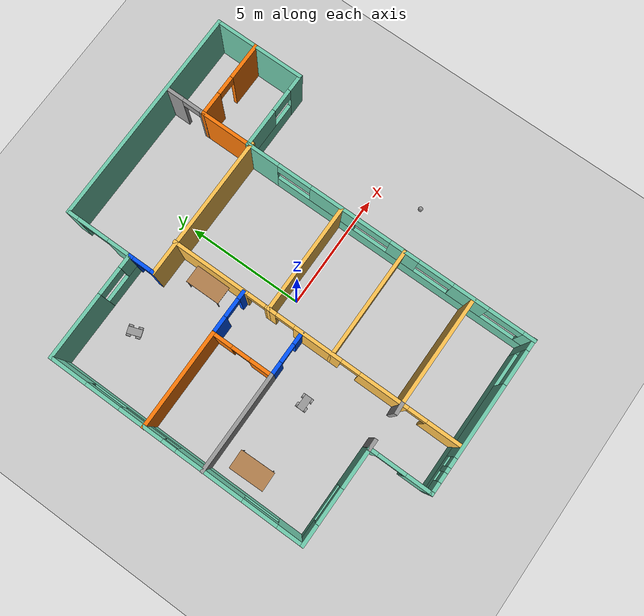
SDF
<sdf version="1.6">
 <world name="default">
  <plugin filename="libcollision_map_creator.so" name="collision_map_creator"/>
  <light name="sun" type="directional">
   <pose>0 0 10 0 -0 0</pose>
   <diffuse>0.8 0.8 0.8 1</diffuse>
   <specular>0.2 0.2 0.2 1</specular>
   <attenuation>
    <range>1000</range>
    <constant>0.9</constant>
    <linear>0.01</linear>
    <quadratic>0.001</quadratic>
   </attenuation>
   <direction>-0.5 0.1 -0.9</direction>
  </light>
  <model name="ground_plane">
   <static>1</static>
   <link name="link">
    <collision name="collision">
     <geometry><plane><normal>0 0 1</normal><size>100 100</size></plane></geometry>
     <surface><friction><ode><mu>100</mu><mu2>50</mu2></ode></friction></surface>
    </collision>
    <visual name="visual">
     <cast_shadows>0</cast_shadows>
     <geometry><plane><normal>0 0 1</normal><size>100 100</size></plane></geometry>
     <material>
      <script><uri>file://media/materials/scripts/gazebo.material</uri><name>Gazebo/Grey</name></script>
     </material>
    </visual>
   </link>
  </model>
  <gravity>0 0 -9.8</gravity>
  <magnetic_field>6e-06 2.3e-05 -4.2e-05</magnetic_field>
  <atmosphere type="adiabatic"/>
  <physics name="default_physics" default="0" type="ode">
   <max_step_size>0.001</max_step_size>
   <real_time_factor>1</real_time_factor>
   <real_time_update_rate>1000</real_time_update_rate>
  </physics>
  <scene><ambient>0.4 0.4 0.4 1</ambient><background>0.7 0.7 0.7 1</background><shadows>1</shadows></scene>
  <spherical_coordinates>
   <surface_model>EARTH_WGS84</surface_model>
   <latitude_deg>0</latitude_deg>
   <longitude_deg>0</longitude_deg>
   <elevation>0</elevation>
   <heading_deg>0</heading_deg>
  </spherical_coordinates>
  <model name="table">
   <static>1</static>
   <link name="link">
    <collision name="surface">
     <pose>0 0 1 0 -0 0</pose>
     <geometry><box><size>1.5 0.8 0.03</size></box></geometry>
     <surface><friction><ode><mu>0.6</mu><mu2>0.6</mu2></ode></friction></surface>
    </collision>
    <visual name="visual1">
     <pose>0 0 1 0 -0 0</pose>
     <geometry><box><size>1.5 0.8 0.03</size></box></geometry>
     <material>
      <script><uri>file://media/materials/scripts/gazebo.material</uri><name>Gazebo/Wood</name></script>
     </material>
    </visual>
    <collision name="front_left_leg">
     <pose>0.68 0.38 0.5 0 -0 0</pose>
     <geometry><cylinder><radius>0.02</radius><length>1</length></cylinder></geometry>
    </collision>
    <visual name="front_left_leg">
     <pose>0.68 0.38 0.5 0 -0 0</pose>
     <geometry><cylinder><radius>0.02</radius><length>1</length></cylinder></geometry>
     <material>
      <script><uri>file://media/materials/scripts/gazebo.material</uri><name>Gazebo/Grey</name></script>
     </material>
    </visual>
    <collision name="front_right_leg">
     <pose>0.68 -0.38 0.5 0 -0 0</pose>
     <geometry><cylinder><radius>0.02</radius><length>1</length></cylinder></geometry>
    </collision>
    <visual name="front_right_leg">
     <pose>0.68 -0.38 0.5 0 -0 0</pose>
     <geometry><cylinder><radius>0.02</radius><length>1</length></cylinder></geometry>
     <material>
      <script><uri>file://media/materials/scripts/gazebo.material</uri><name>Gazebo/Grey</name></script>
     </material>
    </visual>
    <collision name="back_right_leg">
     <pose>-0.68 -0.38 0.5 0 -0 0</pose>
     <geometry><cylinder><radius>0.02</radius><length>1</length></cylinder></geometry>
    </collision>
    <visual name="back_right_leg">
     <pose>-0.68 -0.38 0.5 0 -0 0</pose>
     <geometry><cylinder><radius>0.02</radius><length>1</length></cylinder></geometry>
     <material>
      <script><uri>file://media/materials/scripts/gazebo.material</uri><name>Gazebo/Grey</name></script>
     </material>
    </visual>
    <collision name="back_left_leg">
     <pose>-0.68 0.38 0.5 0 -0 0</pose>
     <geometry><cylinder><radius>0.02</radius><length>1</length></cylinder></geometry>
    </collision>
    <visual name="back_left_leg">
     <pose>-0.68 0.38 0.5 0 -0 0</pose>
     <geometry><cylinder><radius>0.02</radius><length>1</length></cylinder></geometry>
     <material>
      <script><uri>file://media/materials/scripts/gazebo.material</uri><name>Gazebo/Grey</name></script>
     </material>
    </visual>
   </link>
   <pose>-1.52221 3.05616 0 0 0 -1.56655</pose>
  </model>
  <model name="table_0">
   <static>1</static>
   <link name="link">
    <collision name="surface">
     <pose>0 0 1 0 -0 0</pose>
     <geometry><box><size>1.5 0.8 0.03</size></box></geometry>
     <surface><friction><ode><mu>0.6</mu><mu2>0.6</mu2></ode></friction></surface>
    </collision>
    <visual name="visual1">
     <pose>0 0 1 0 -0 0</pose>
     <geometry><box><size>1.5 0.8 0.03</size></box></geometry>
     <material>
      <script><uri>file://media/materials/scripts/gazebo.material</uri><name>Gazebo/Wood</name></script>
     </material>
    </visual>
    <collision name="front_left_leg">
     <pose>0.68 0.38 0.5 0 -0 0</pose>
     <geometry><cylinder><radius>0.02</radius><length>1</length></cylinder></geometry>
    </collision>
    <visual name="front_left_leg">
     <pose>0.68 0.38 0.5 0 -0 0</pose>
     <geometry><cylinder><radius>0.02</radius><length>1</length></cylinder></geometry>
     <material>
      <script><uri>file://media/materials/scripts/gazebo.material</uri><name>Gazebo/Grey</name></script>
     </material>
    </visual>
    <collision name="front_right_leg">
     <pose>0.68 -0.38 0.5 0 -0 0</pose>
     <geometry><cylinder><radius>0.02</radius><length>1</length></cylinder></geometry>
    </collision>
    <visual name="front_right_leg">
     <pose>0.68 -0.38 0.5 0 -0 0</pose>
     <geometry><cylinder><radius>0.02</radius><length>1</length></cylinder></geometry>
     <material>
      <script><uri>file://media/materials/scripts/gazebo.material</uri><name>Gazebo/Grey</name></script>
     </material>
    </visual>
    <collision name="back_right_leg">
     <pose>-0.68 -0.38 0.5 0 -0 0</pose>
     <geometry><cylinder><radius>0.02</radius><length>1</length></cylinder></geometry>
    </collision>
    <visual name="back_right_leg">
     <pose>-0.68 -0.38 0.5 0 -0 0</pose>
     <geometry><cylinder><radius>0.02</radius><length>1</length></cylinder></geometry>
     <material>
      <script><uri>file://media/materials/scripts/gazebo.material</uri><name>Gazebo/Grey</name></script>
     </material>
    </visual>
    <collision name="back_left_leg">
     <pose>-0.68 0.38 0.5 0 -0 0</pose>
     <geometry><cylinder><radius>0.02</radius><length>1</length></cylinder></geometry>
    </collision>
    <visual name="back_left_leg">
     <pose>-0.68 0.38 0.5 0 -0 0</pose>
     <geometry><cylinder><radius>0.02</radius><length>1</length></cylinder></geometry>
     <material>
      <script><uri>file://media/materials/scripts/gazebo.material</uri><name>Gazebo/Grey</name></script>
     </material>
    </visual>
   </link>
   <pose>-6.15414 -2.39561 0 0 0 -1.54951</pose>
  </model>
  <model name="4wRobot">
   <link name="link_0">
    <pose>0 9e-06 0 0 -0 1.5707</pose>
    <inertial>
     <mass>1</mass>
     <inertia>
      <ixx>0.166667</ixx>
      <ixy>0</ixy>
      <ixz>0</ixz>
      <iyy>0.166667</iyy>
      <iyz>0</iyz>
      <izz>0.166667</izz>
     </inertia>
     <pose>0 0 0.08 0 -0 0</pose>
    </inertial>
    <visual name="visual">
     <geometry><box><size>0.3 0.6 0.08</size></box></geometry>
     <material>
      <lighting>1</lighting>
      <script><uri>file://media/materials/scripts/gazebo.material</uri><name>Gazebo/Grey</name></script>
      <shader type="pixel"><normal_map>__default__</normal_map></shader>
      <ambient>0.3 0.3 0.3 1</ambient>
      <diffuse>0.7 0.7 0.7 1</diffuse>
      <specular>0.01 0.01 0.01 1</specular>
      <emissive>0 0 0 1</emissive>
     </material>
    </visual>
    <collision name="collision">
     <geometry><box><size>0.3 0.6 0.08</size></box></geometry>
     <surface>
      <friction>
       <ode><mu>1</mu><mu2>1</mu2><fdir1>0 0 0</fdir1><slip1>0</slip1><slip2>0</slip2></ode>
       <torsional>
        <coefficient>1</coefficient>
        <patch_radius>0</patch_radius>
        <surface_radius>0</surface_radius>
        <use_patch_radius>1</use_patch_radius>
        <ode><slip>0</slip></ode>
       </torsional>
      </friction>
      <bounce><restitution_coefficient>0</restitution_coefficient><threshold>1e+06</threshold></bounce>
      <contact>
       <collide_without_contact>0</collide_without_contact>
       <collide_without_contact_bitmask>1</collide_without_contact_bitmask>
       <collide_bitmask>1</collide_bitmask>
       <ode>
        <soft_cfm>0</soft_cfm>
        <soft_erp>0.2</soft_erp>
        <kp>1e+13</kp>
        <kd>1</kd>
        <max_vel>0.01</max_vel>
        <min_depth>0</min_depth>
       </ode>
       <bullet>
        <split_impulse>1</split_impulse>
        <split_impulse_penetration_threshold>-0.01</split_impulse_penetration_threshold>
        <soft_cfm>0</soft_cfm>
        <soft_erp>0.2</soft_erp>
        <kp>1e+13</kp>
        <kd>1</kd>
       </bullet>
      </contact>
     </surface>
    </collision>
   </link>
   <link name="link_3">
    <pose>-0.200015 -0.190034 0 1.5707 -0 0</pose>
    <inertial>
     <mass>1</mass>
     <inertia><ixx>0.145833</ixx><ixy>0</ixy><ixz>0</ixz><iyy>0.145833</iyy><iyz>0</iyz><izz>0.125</izz></inertia>
    </inertial>
    <visual name="visual">
     <geometry><cylinder><radius>0.1</radius><length>0.08</length></cylinder></geometry>
     <material>
      <lighting>1</lighting>
      <script><uri>file://media/materials/scripts/gazebo.material</uri><name>Gazebo/Grey</name></script>
      <shader type="pixel"><normal_map>__default__</normal_map></shader>
      <ambient>0.3 0.3 0.3 1</ambient>
      <diffuse>0.7 0.7 0.7 1</diffuse>
      <specular>0.01 0.01 0.01 1</specular>
      <emissive>0 0 0 1</emissive>
     </material>
    </visual>
    <collision name="collision">
     <geometry><cylinder><radius>0.1</radius><length>0.08</length></cylinder></geometry>
     <surface>
      <friction>
       <ode><mu>1</mu><mu2>1</mu2><fdir1>0 0 0</fdir1><slip1>0</slip1><slip2>0</slip2></ode>
       <torsional>
        <coefficient>1</coefficient>
        <patch_radius>0</patch_radius>
        <surface_radius>0</surface_radius>
        <use_patch_radius>1</use_patch_radius>
        <ode><slip>0</slip></ode>
       </torsional>
      </friction>
      <bounce><restitution_coefficient>0</restitution_coefficient><threshold>1e+06</threshold></bounce>
      <contact>
       <collide_without_contact>0</collide_without_contact>
       <collide_without_contact_bitmask>1</collide_without_contact_bitmask>
       <collide_bitmask>1</collide_bitmask>
       <ode>
        <soft_cfm>0</soft_cfm>
        <soft_erp>0.2</soft_erp>
        <kp>1e+13</kp>
        <kd>1</kd>
        <max_vel>0.01</max_vel>
        <min_depth>0</min_depth>
       </ode>
       <bullet>
        <split_impulse>1</split_impulse>
        <split_impulse_penetration_threshold>-0.01</split_impulse_penetration_threshold>
        <soft_cfm>0</soft_cfm>
        <soft_erp>0.2</soft_erp>
        <kp>1e+13</kp>
        <kd>1</kd>
       </bullet>
      </contact>
     </surface>
    </collision>
   </link>
   <link name="link_3_clone">
    <pose>-0.200015 0.190048 0 1.5707 -0 0</pose>
    <inertial>
     <mass>1</mass>
     <inertia><ixx>0.145833</ixx><ixy>0</ixy><ixz>0</ixz><iyy>0.145833</iyy><iyz>0</iyz><izz>0.125</izz></inertia>
    </inertial>
    <visual name="visual">
     <geometry><cylinder><radius>0.1</radius><length>0.08</length></cylinder></geometry>
     <material>
      <lighting>1</lighting>
      <script><uri>file://media/materials/scripts/gazebo.material</uri><name>Gazebo/Grey</name></script>
      <shader type="pixel"><normal_map>__default__</normal_map></shader>
      <ambient>0.3 0.3 0.3 1</ambient>
      <diffuse>0.7 0.7 0.7 1</diffuse>
      <specular>0.01 0.01 0.01 1</specular>
      <emissive>0 0 0 1</emissive>
     </material>
    </visual>
    <collision name="collision">
     <geometry><cylinder><radius>0.1</radius><length>0.08</length></cylinder></geometry>
     <surface>
      <friction>
       <ode><mu>1</mu><mu2>1</mu2><fdir1>0 0 0</fdir1><slip1>0</slip1><slip2>0</slip2></ode>
       <torsional>
        <coefficient>1</coefficient>
        <patch_radius>0</patch_radius>
        <surface_radius>0</surface_radius>
        <use_patch_radius>1</use_patch_radius>
        <ode><slip>0</slip></ode>
       </torsional>
      </friction>
      <bounce><restitution_coefficient>0</restitution_coefficient><threshold>1e+06</threshold></bounce>
      <contact>
       <collide_without_contact>0</collide_without_contact>
       <collide_without_contact_bitmask>1</collide_without_contact_bitmask>
       <collide_bitmask>1</collide_bitmask>
       <ode>
        <soft_cfm>0</soft_cfm>
        <soft_erp>0.2</soft_erp>
        <kp>1e+13</kp>
        <kd>1</kd>
        <max_vel>0.01</max_vel>
        <min_depth>0</min_depth>
       </ode>
       <bullet>
        <split_impulse>1</split_impulse>
        <split_impulse_penetration_threshold>-0.01</split_impulse_penetration_threshold>
        <soft_cfm>0</soft_cfm>
        <soft_erp>0.2</soft_erp>
        <kp>1e+13</kp>
        <kd>1</kd>
       </bullet>
      </contact>
     </surface>
    </collision>
   </link>
   <link name="link_3_clone_0">
    <pose>0.200015 -0.19003 0 1.5707 -0 0</pose>
    <inertial>
     <mass>1</mass>
     <inertia><ixx>0.145833</ixx><ixy>0</ixy><ixz>0</ixz><iyy>0.145833</iyy><iyz>0</iyz><izz>0.125</izz></inertia>
    </inertial>
    <visual name="visual">
     <geometry><cylinder><radius>0.1</radius><length>0.08</length></cylinder></geometry>
     <material>
      <lighting>1</lighting>
      <script><uri>file://media/materials/scripts/gazebo.material</uri><name>Gazebo/Grey</name></script>
      <shader type="pixel"><normal_map>__default__</normal_map></shader>
      <ambient>0.3 0.3 0.3 1</ambient>
      <diffuse>0.7 0.7 0.7 1</diffuse>
      <specular>0.01 0.01 0.01 1</specular>
      <emissive>0 0 0 1</emissive>
     </material>
    </visual>
    <collision name="collision">
     <geometry><cylinder><radius>0.1</radius><length>0.08</length></cylinder></geometry>
     <surface>
      <friction>
       <ode><mu>1</mu><mu2>1</mu2><fdir1>0 0 0</fdir1><slip1>0</slip1><slip2>0</slip2></ode>
       <torsional>
        <coefficient>1</coefficient>
        <patch_radius>0</patch_radius>
        <surface_radius>0</surface_radius>
        <use_patch_radius>1</use_patch_radius>
        <ode><slip>0</slip></ode>
       </torsional>
      </friction>
      <bounce><restitution_coefficient>0</restitution_coefficient><threshold>1e+06</threshold></bounce>
      <contact>
       <collide_without_contact>0</collide_without_contact>
       <collide_without_contact_bitmask>1</collide_without_contact_bitmask>
       <collide_bitmask>1</collide_bitmask>
       <ode>
        <soft_cfm>0</soft_cfm>
        <soft_erp>0.2</soft_erp>
        <kp>1e+13</kp>
        <kd>1</kd>
        <max_vel>0.01</max_vel>
        <min_depth>0</min_depth>
       </ode>
       <bullet>
        <split_impulse>1</split_impulse>
        <split_impulse_penetration_threshold>-0.01</split_impulse_penetration_threshold>
        <soft_cfm>0</soft_cfm>
        <soft_erp>0.2</soft_erp>
        <kp>1e+13</kp>
        <kd>1</kd>
       </bullet>
      </contact>
     </surface>
    </collision>
   </link>
   <link name="link_3_clone_1">
    <pose>0.200015 0.190048 0 1.5707 -0 0</pose>
    <inertial>
     <mass>1</mass>
     <inertia><ixx>0.145833</ixx><ixy>0</ixy><ixz>0</ixz><iyy>0.145833</iyy><iyz>0</iyz><izz>0.125</izz></inertia>
    </inertial>
    <visual name="visual">
     <geometry><cylinder><radius>0.1</radius><length>0.08</length></cylinder></geometry>
     <material>
      <lighting>1</lighting>
      <script><uri>file://media/materials/scripts/gazebo.material</uri><name>Gazebo/Grey</name></script>
      <shader type="pixel"><normal_map>__default__</normal_map></shader>
      <ambient>0.3 0.3 0.3 1</ambient>
      <diffuse>0.7 0.7 0.7 1</diffuse>
      <specular>0.01 0.01 0.01 1</specular>
      <emissive>0 0 0 1</emissive>
     </material>
    </visual>
    <collision name="collision">
     <geometry><cylinder><radius>0.1</radius><length>0.08</length></cylinder></geometry>
     <surface>
      <friction>
       <ode><mu>1</mu><mu2>1</mu2><fdir1>0 0 0</fdir1><slip1>0</slip1><slip2>0</slip2></ode>
       <torsional>
        <coefficient>1</coefficient>
        <patch_radius>0</patch_radius>
        <surface_radius>0</surface_radius>
        <use_patch_radius>1</use_patch_radius>
        <ode><slip>0</slip></ode>
       </torsional>
      </friction>
      <bounce><restitution_coefficient>0</restitution_coefficient><threshold>1e+06</threshold></bounce>
      <contact>
       <collide_without_contact>0</collide_without_contact>
       <collide_without_contact_bitmask>1</collide_without_contact_bitmask>
       <collide_bitmask>1</collide_bitmask>
       <ode>
        <soft_cfm>0</soft_cfm>
        <soft_erp>0.2</soft_erp>
        <kp>1e+13</kp>
        <kd>1</kd>
        <max_vel>0.01</max_vel>
        <min_depth>0</min_depth>
       </ode>
       <bullet>
        <split_impulse>1</split_impulse>
        <split_impulse_penetration_threshold>-0.01</split_impulse_penetration_threshold>
        <soft_cfm>0</soft_cfm>
        <soft_erp>0.2</soft_erp>
        <kp>1e+13</kp>
        <kd>1</kd>
       </bullet>
      </contact>
     </surface>
    </collision>
   </link>
   <joint name="link_0_JOINT_3" type="revolute">
    <parent>link_0</parent>
    <child>link_3</child>
    <axis>
     <xyz>1 0 0</xyz>
     <use_parent_model_frame>0</use_parent_model_frame>
     <limit>
      <lower>-1.79769e+308</lower>
      <upper>1.79769e+308</upper>
      <effort>-1</effort>
      <velocity>-1</velocity>
     </limit>
     <dynamics>
      <spring_reference>0</spring_reference>
      <spring_stiffness>0</spring_stiffness>
      <damping>0</damping>
     </dynamics>
    </axis>
    <physics>
     <ode><limit><cfm>0</cfm><erp>0.2</erp></limit><suspension><cfm>0</cfm><erp>0.2</erp></suspension></ode>
    </physics>
   </joint>
   <joint name="link_0_JOINT_4" type="revolute">
    <parent>link_0</parent>
    <child>link_3_clone</child>
    <axis>
     <xyz>1 0 0</xyz>
     <use_parent_model_frame>0</use_parent_model_frame>
     <limit>
      <lower>-1.79769e+308</lower>
      <upper>1.79769e+308</upper>
      <effort>-1</effort>
      <velocity>-1</velocity>
     </limit>
     <dynamics>
      <spring_reference>0</spring_reference>
      <spring_stiffness>0</spring_stiffness>
      <damping>0</damping>
     </dynamics>
    </axis>
    <physics>
     <ode><limit><cfm>0</cfm><erp>0.2</erp></limit><suspension><cfm>0</cfm><erp>0.2</erp></suspension></ode>
    </physics>
   </joint>
   <joint name="link_0_JOINT_5" type="revolute">
    <parent>link_0</parent>
    <child>link_3_clone_0</child>
    <axis>
     <xyz>1 0 0</xyz>
     <use_parent_model_frame>0</use_parent_model_frame>
     <limit>
      <lower>-1.79769e+308</lower>
      <upper>1.79769e+308</upper>
      <effort>-1</effort>
      <velocity>-1</velocity>
     </limit>
     <dynamics>
      <spring_reference>0</spring_reference>
      <spring_stiffness>0</spring_stiffness>
      <damping>0</damping>
     </dynamics>
    </axis>
    <physics>
     <ode><limit><cfm>0</cfm><erp>0.2</erp></limit><suspension><cfm>0</cfm><erp>0.2</erp></suspension></ode>
    </physics>
   </joint>
   <joint name="link_0_JOINT_6" type="revolute">
    <parent>link_0</parent>
    <child>link_3_clone_1</child>
    <axis>
     <xyz>1 0 0</xyz>
     <use_parent_model_frame>0</use_parent_model_frame>
     <limit>
      <lower>-1.79769e+308</lower>
      <upper>1.79769e+308</upper>
      <effort>-1</effort>
      <velocity>-1</velocity>
     </limit>
     <dynamics>
      <spring_reference>0</spring_reference>
      <spring_stiffness>0</spring_stiffness>
      <damping>0</damping>
     </dynamics>
    </axis>
    <physics>
     <ode><limit><cfm>0</cfm><erp>0.2</erp></limit><suspension><cfm>0</cfm><erp>0.2</erp></suspension></ode>
    </physics>
   </joint>
   <joint name="link_0_JOINT_7" type="revolute">
    <parent>link_0</parent>
    <child>link_3</child>
    <axis>
     <xyz>1 0 0</xyz>
     <use_parent_model_frame>0</use_parent_model_frame>
     <limit>
      <lower>-1.79769e+308</lower>
      <upper>1.79769e+308</upper>
      <effort>-1</effort>
      <velocity>-1</velocity>
     </limit>
     <dynamics>
      <spring_reference>0</spring_reference>
      <spring_stiffness>0</spring_stiffness>
      <damping>0</damping>
     </dynamics>
    </axis>
    <physics>
     <ode><limit><cfm>0</cfm><erp>0.2</erp></limit><suspension><cfm>0</cfm><erp>0.2</erp></suspension></ode>
    </physics>
   </joint>
   <static>0</static>
   <pose>-2.99781 -2.52289 0.1 0 0 -0.00024</pose>
  </model>
  <model name="4wRobot_clone">
   <link name="link_0">
    <pose>0 9e-06 0 0 -0 1.5707</pose>
    <inertial>
     <mass>1</mass>
     <inertia>
      <ixx>0.166667</ixx>
      <ixy>0</ixy>
      <ixz>0</ixz>
      <iyy>0.166667</iyy>
      <iyz>0</iyz>
      <izz>0.166667</izz>
     </inertia>
     <pose>0 0 0.08 0 -0 0</pose>
    </inertial>
    <visual name="visual">
     <geometry><box><size>0.3 0.6 0.08</size></box></geometry>
     <material>
      <lighting>1</lighting>
      <script><uri>file://media/materials/scripts/gazebo.material</uri><name>Gazebo/Grey</name></script>
      <shader type="pixel"><normal_map>__default__</normal_map></shader>
      <ambient>0.3 0.3 0.3 1</ambient>
      <diffuse>0.7 0.7 0.7 1</diffuse>
      <specular>0.01 0.01 0.01 1</specular>
      <emissive>0 0 0 1</emissive>
     </material>
    </visual>
    <collision name="collision">
     <geometry><box><size>0.3 0.6 0.08</size></box></geometry>
     <surface>
      <friction>
       <ode><mu>1</mu><mu2>1</mu2><fdir1>0 0 0</fdir1><slip1>0</slip1><slip2>0</slip2></ode>
       <torsional>
        <coefficient>1</coefficient>
        <patch_radius>0</patch_radius>
        <surface_radius>0</surface_radius>
        <use_patch_radius>1</use_patch_radius>
        <ode><slip>0</slip></ode>
       </torsional>
      </friction>
      <bounce><restitution_coefficient>0</restitution_coefficient><threshold>1e+06</threshold></bounce>
      <contact>
       <collide_without_contact>0</collide_without_contact>
       <collide_without_contact_bitmask>1</collide_without_contact_bitmask>
       <collide_bitmask>1</collide_bitmask>
       <ode>
        <soft_cfm>0</soft_cfm>
        <soft_erp>0.2</soft_erp>
        <kp>1e+13</kp>
        <kd>1</kd>
        <max_vel>0.01</max_vel>
        <min_depth>0</min_depth>
       </ode>
       <bullet>
        <split_impulse>1</split_impulse>
        <split_impulse_penetration_threshold>-0.01</split_impulse_penetration_threshold>
        <soft_cfm>0</soft_cfm>
        <soft_erp>0.2</soft_erp>
        <kp>1e+13</kp>
        <kd>1</kd>
       </bullet>
      </contact>
     </surface>
    </collision>
   </link>
   <link name="link_3">
    <pose>-0.200015 -0.190034 0 1.5707 -0 0</pose>
    <inertial>
     <mass>1</mass>
     <inertia><ixx>0.145833</ixx><ixy>0</ixy><ixz>0</ixz><iyy>0.145833</iyy><iyz>0</iyz><izz>0.125</izz></inertia>
    </inertial>
    <visual name="visual">
     <geometry><cylinder><radius>0.1</radius><length>0.08</length></cylinder></geometry>
     <material>
      <lighting>1</lighting>
      <script><uri>file://media/materials/scripts/gazebo.material</uri><name>Gazebo/Grey</name></script>
      <shader type="pixel"><normal_map>__default__</normal_map></shader>
      <ambient>0.3 0.3 0.3 1</ambient>
      <diffuse>0.7 0.7 0.7 1</diffuse>
      <specular>0.01 0.01 0.01 1</specular>
      <emissive>0 0 0 1</emissive>
     </material>
    </visual>
    <collision name="collision">
     <geometry><cylinder><radius>0.1</radius><length>0.08</length></cylinder></geometry>
     <surface>
      <friction>
       <ode><mu>1</mu><mu2>1</mu2><fdir1>0 0 0</fdir1><slip1>0</slip1><slip2>0</slip2></ode>
       <torsional>
        <coefficient>1</coefficient>
        <patch_radius>0</patch_radius>
        <surface_radius>0</surface_radius>
        <use_patch_radius>1</use_patch_radius>
        <ode><slip>0</slip></ode>
       </torsional>
      </friction>
      <bounce><restitution_coefficient>0</restitution_coefficient><threshold>1e+06</threshold></bounce>
      <contact>
       <collide_without_contact>0</collide_without_contact>
       <collide_without_contact_bitmask>1</collide_without_contact_bitmask>
       <collide_bitmask>1</collide_bitmask>
       <ode>
        <soft_cfm>0</soft_cfm>
        <soft_erp>0.2</soft_erp>
        <kp>1e+13</kp>
        <kd>1</kd>
        <max_vel>0.01</max_vel>
        <min_depth>0</min_depth>
       </ode>
       <bullet>
        <split_impulse>1</split_impulse>
        <split_impulse_penetration_threshold>-0.01</split_impulse_penetration_threshold>
        <soft_cfm>0</soft_cfm>
        <soft_erp>0.2</soft_erp>
        <kp>1e+13</kp>
        <kd>1</kd>
       </bullet>
      </contact>
     </surface>
    </collision>
   </link>
   <link name="link_3_clone">
    <pose>-0.200015 0.190048 0 1.5707 -0 0</pose>
    <inertial>
     <mass>1</mass>
     <inertia><ixx>0.145833</ixx><ixy>0</ixy><ixz>0</ixz><iyy>0.145833</iyy><iyz>0</iyz><izz>0.125</izz></inertia>
    </inertial>
    <visual name="visual">
     <geometry><cylinder><radius>0.1</radius><length>0.08</length></cylinder></geometry>
     <material>
      <lighting>1</lighting>
      <script><uri>file://media/materials/scripts/gazebo.material</uri><name>Gazebo/Grey</name></script>
      <shader type="pixel"><normal_map>__default__</normal_map></shader>
      <ambient>0.3 0.3 0.3 1</ambient>
      <diffuse>0.7 0.7 0.7 1</diffuse>
      <specular>0.01 0.01 0.01 1</specular>
      <emissive>0 0 0 1</emissive>
     </material>
    </visual>
    <collision name="collision">
     <geometry><cylinder><radius>0.1</radius><length>0.08</length></cylinder></geometry>
     <surface>
      <friction>
       <ode><mu>1</mu><mu2>1</mu2><fdir1>0 0 0</fdir1><slip1>0</slip1><slip2>0</slip2></ode>
       <torsional>
        <coefficient>1</coefficient>
        <patch_radius>0</patch_radius>
        <surface_radius>0</surface_radius>
        <use_patch_radius>1</use_patch_radius>
        <ode><slip>0</slip></ode>
       </torsional>
      </friction>
      <bounce><restitution_coefficient>0</restitution_coefficient><threshold>1e+06</threshold></bounce>
      <contact>
       <collide_without_contact>0</collide_without_contact>
       <collide_without_contact_bitmask>1</collide_without_contact_bitmask>
       <collide_bitmask>1</collide_bitmask>
       <ode>
        <soft_cfm>0</soft_cfm>
        <soft_erp>0.2</soft_erp>
        <kp>1e+13</kp>
        <kd>1</kd>
        <max_vel>0.01</max_vel>
        <min_depth>0</min_depth>
       </ode>
       <bullet>
        <split_impulse>1</split_impulse>
        <split_impulse_penetration_threshold>-0.01</split_impulse_penetration_threshold>
        <soft_cfm>0</soft_cfm>
        <soft_erp>0.2</soft_erp>
        <kp>1e+13</kp>
        <kd>1</kd>
       </bullet>
      </contact>
     </surface>
    </collision>
   </link>
   <link name="link_3_clone_0">
    <pose>0.200015 -0.19003 0 1.5707 -0 0</pose>
    <inertial>
     <mass>1</mass>
     <inertia><ixx>0.145833</ixx><ixy>0</ixy><ixz>0</ixz><iyy>0.145833</iyy><iyz>0</iyz><izz>0.125</izz></inertia>
    </inertial>
    <visual name="visual">
     <geometry><cylinder><radius>0.1</radius><length>0.08</length></cylinder></geometry>
     <material>
      <lighting>1</lighting>
      <script><uri>file://media/materials/scripts/gazebo.material</uri><name>Gazebo/Grey</name></script>
      <shader type="pixel"><normal_map>__default__</normal_map></shader>
      <ambient>0.3 0.3 0.3 1</ambient>
      <diffuse>0.7 0.7 0.7 1</diffuse>
      <specular>0.01 0.01 0.01 1</specular>
      <emissive>0 0 0 1</emissive>
     </material>
    </visual>
    <collision name="collision">
     <geometry><cylinder><radius>0.1</radius><length>0.08</length></cylinder></geometry>
     <surface>
      <friction>
       <ode><mu>1</mu><mu2>1</mu2><fdir1>0 0 0</fdir1><slip1>0</slip1><slip2>0</slip2></ode>
       <torsional>
        <coefficient>1</coefficient>
        <patch_radius>0</patch_radius>
        <surface_radius>0</surface_radius>
        <use_patch_radius>1</use_patch_radius>
        <ode><slip>0</slip></ode>
       </torsional>
      </friction>
      <bounce><restitution_coefficient>0</restitution_coefficient><threshold>1e+06</threshold></bounce>
      <contact>
       <collide_without_contact>0</collide_without_contact>
       <collide_without_contact_bitmask>1</collide_without_contact_bitmask>
       <collide_bitmask>1</collide_bitmask>
       <ode>
        <soft_cfm>0</soft_cfm>
        <soft_erp>0.2</soft_erp>
        <kp>1e+13</kp>
        <kd>1</kd>
        <max_vel>0.01</max_vel>
        <min_depth>0</min_depth>
       </ode>
       <bullet>
        <split_impulse>1</split_impulse>
        <split_impulse_penetration_threshold>-0.01</split_impulse_penetration_threshold>
        <soft_cfm>0</soft_cfm>
        <soft_erp>0.2</soft_erp>
        <kp>1e+13</kp>
        <kd>1</kd>
       </bullet>
      </contact>
     </surface>
    </collision>
   </link>
   <link name="link_3_clone_1">
    <pose>0.200015 0.190048 0 1.5707 -0 0</pose>
    <inertial>
     <mass>1</mass>
     <inertia><ixx>0.145833</ixx><ixy>0</ixy><ixz>0</ixz><iyy>0.145833</iyy><iyz>0</iyz><izz>0.125</izz></inertia>
    </inertial>
    <visual name="visual">
     <geometry><cylinder><radius>0.1</radius><length>0.08</length></cylinder></geometry>
     <material>
      <lighting>1</lighting>
      <script><uri>file://media/materials/scripts/gazebo.material</uri><name>Gazebo/Grey</name></script>
      <shader type="pixel"><normal_map>__default__</normal_map></shader>
      <ambient>0.3 0.3 0.3 1</ambient>
      <diffuse>0.7 0.7 0.7 1</diffuse>
      <specular>0.01 0.01 0.01 1</specular>
      <emissive>0 0 0 1</emissive>
     </material>
    </visual>
    <collision name="collision">
     <geometry><cylinder><radius>0.1</radius><length>0.08</length></cylinder></geometry>
     <surface>
      <friction>
       <ode><mu>1</mu><mu2>1</mu2><fdir1>0 0 0</fdir1><slip1>0</slip1><slip2>0</slip2></ode>
       <torsional>
        <coefficient>1</coefficient>
        <patch_radius>0</patch_radius>
        <surface_radius>0</surface_radius>
        <use_patch_radius>1</use_patch_radius>
        <ode><slip>0</slip></ode>
       </torsional>
      </friction>
      <bounce><restitution_coefficient>0</restitution_coefficient><threshold>1e+06</threshold></bounce>
      <contact>
       <collide_without_contact>0</collide_without_contact>
       <collide_without_contact_bitmask>1</collide_without_contact_bitmask>
       <collide_bitmask>1</collide_bitmask>
       <ode>
        <soft_cfm>0</soft_cfm>
        <soft_erp>0.2</soft_erp>
        <kp>1e+13</kp>
        <kd>1</kd>
        <max_vel>0.01</max_vel>
        <min_depth>0</min_depth>
       </ode>
       <bullet>
        <split_impulse>1</split_impulse>
        <split_impulse_penetration_threshold>-0.01</split_impulse_penetration_threshold>
        <soft_cfm>0</soft_cfm>
        <soft_erp>0.2</soft_erp>
        <kp>1e+13</kp>
        <kd>1</kd>
       </bullet>
      </contact>
     </surface>
    </collision>
   </link>
   <joint name="link_0_JOINT_3" type="revolute">
    <parent>link_0</parent>
    <child>link_3</child>
    <axis>
     <xyz>1 0 0</xyz>
     <use_parent_model_frame>0</use_parent_model_frame>
     <limit>
      <lower>-1.79769e+308</lower>
      <upper>1.79769e+308</upper>
      <effort>-1</effort>
      <velocity>-1</velocity>
     </limit>
     <dynamics>
      <spring_reference>0</spring_reference>
      <spring_stiffness>0</spring_stiffness>
      <damping>0</damping>
     </dynamics>
    </axis>
    <physics>
     <ode><limit><cfm>0</cfm><erp>0.2</erp></limit><suspension><cfm>0</cfm><erp>0.2</erp></suspension></ode>
    </physics>
   </joint>
   <joint name="link_0_JOINT_4" type="revolute">
    <parent>link_0</parent>
    <child>link_3_clone</child>
    <axis>
     <xyz>1 0 0</xyz>
     <use_parent_model_frame>0</use_parent_model_frame>
     <limit>
      <lower>-1.79769e+308</lower>
      <upper>1.79769e+308</upper>
      <effort>-1</effort>
      <velocity>-1</velocity>
     </limit>
     <dynamics>
      <spring_reference>0</spring_reference>
      <spring_stiffness>0</spring_stiffness>
      <damping>0</damping>
     </dynamics>
    </axis>
    <physics>
     <ode><limit><cfm>0</cfm><erp>0.2</erp></limit><suspension><cfm>0</cfm><erp>0.2</erp></suspension></ode>
    </physics>
   </joint>
   <joint name="link_0_JOINT_5" type="revolute">
    <parent>link_0</parent>
    <child>link_3_clone_0</child>
    <axis>
     <xyz>1 0 0</xyz>
     <use_parent_model_frame>0</use_parent_model_frame>
     <limit>
      <lower>-1.79769e+308</lower>
      <upper>1.79769e+308</upper>
      <effort>-1</effort>
      <velocity>-1</velocity>
     </limit>
     <dynamics>
      <spring_reference>0</spring_reference>
      <spring_stiffness>0</spring_stiffness>
      <damping>0</damping>
     </dynamics>
    </axis>
    <physics>
     <ode><limit><cfm>0</cfm><erp>0.2</erp></limit><suspension><cfm>0</cfm><erp>0.2</erp></suspension></ode>
    </physics>
   </joint>
   <joint name="link_0_JOINT_6" type="revolute">
    <parent>link_0</parent>
    <child>link_3_clone_1</child>
    <axis>
     <xyz>1 0 0</xyz>
     <use_parent_model_frame>0</use_parent_model_frame>
     <limit>
      <lower>-1.79769e+308</lower>
      <upper>1.79769e+308</upper>
      <effort>-1</effort>
      <velocity>-1</velocity>
     </limit>
     <dynamics>
      <spring_reference>0</spring_reference>
      <spring_stiffness>0</spring_stiffness>
      <damping>0</damping>
     </dynamics>
    </axis>
    <physics>
     <ode><limit><cfm>0</cfm><erp>0.2</erp></limit><suspension><cfm>0</cfm><erp>0.2</erp></suspension></ode>
    </physics>
   </joint>
   <joint name="link_0_JOINT_7" type="revolute">
    <parent>link_0</parent>
    <child>link_3</child>
    <axis>
     <xyz>1 0 0</xyz>
     <use_parent_model_frame>0</use_parent_model_frame>
     <limit>
      <lower>-1.79769e+308</lower>
      <upper>1.79769e+308</upper>
      <effort>-1</effort>
      <velocity>-1</velocity>
     </limit>
     <dynamics>
      <spring_reference>0</spring_reference>
      <spring_stiffness>0</spring_stiffness>
      <damping>0</damping>
     </dynamics>
    </axis>
    <physics>
     <ode><limit><cfm>0</cfm><erp>0.2</erp></limit><suspension><cfm>0</cfm><erp>0.2</erp></suspension></ode>
    </physics>
   </joint>
   <static>0</static>
   <pose>-4.6136 4.42664 0.1 0 -0 1.90447</pose>
  </model>
  <model name="Building_0">
   <pose>-0.10939 0.312167 0 0 -0 0</pose>
   <link name="Wall_0">
    <pose>-6.97053 -0.091308 0 0 -0 1.5708</pose>
    <visual name="Wall_0_Visual_0">
     <pose>-5.0443 0 1.25 0 -0 0</pose>
     <geometry><box><size>1.1614 0.15 2.5</size></box></geometry>
     <material>
      <script><uri>file://media/materials/scripts/gazebo.material</uri><name>Gazebo/Grey</name></script>
      <ambient>0.435294 0.796078 0.67451 1</ambient>
     </material>
     <meta><layer>0</layer></meta>
    </visual>
    <collision name="Wall_0_Collision_0">
     <geometry><box><size>1.1614 0.15 2.5</size></box></geometry>
     <pose>-5.0443 0 1.25 0 -0 0</pose>
    </collision>
    <visual name="Wall_0_Visual_1">
     <pose>0.580698 0 0.5 0 -0 0</pose>
     <geometry><box><size>10.0886 0.15 1</size></box></geometry>
     <material>
      <script><uri>file://media/materials/scripts/gazebo.material</uri><name>Gazebo/Grey</name></script>
      <ambient>0.435294 0.796078 0.67451 1</ambient>
     </material>
     <meta><layer>0</layer></meta>
    </visual>
    <collision name="Wall_0_Collision_1">
     <geometry><box><size>10.0886 0.15 1</size></box></geometry>
     <pose>0.580698 0 0.5 0 -0 0</pose>
    </collision>
    <visual name="Wall_0_Visual_2">
     <pose>-1.51094 0 1.75 0 -0 0</pose>
     <geometry><box><size>2.90533 0.15 1.5</size></box></geometry>
     <material>
      <script><uri>file://media/materials/scripts/gazebo.material</uri><name>Gazebo/Grey</name></script>
      <ambient>0.435294 0.796078 0.67451 1</ambient>
     </material>
     <meta><layer>0</layer></meta>
    </visual>
    <collision name="Wall_0_Collision_2">
     <geometry><box><size>2.90533 0.15 1.5</size></box></geometry>
     <pose>-1.51094 0 1.75 0 -0 0</pose>
    </collision>
    <visual name="Wall_0_Visual_3">
     <pose>4.78872 0 1.75 0 -0 0</pose>
     <geometry><box><size>1.67255 0.15 1.5</size></box></geometry>
     <material>
      <script><uri>file://media/materials/scripts/gazebo.material</uri><name>Gazebo/Grey</name></script>
      <ambient>0.435294 0.796078 0.67451 1</ambient>
     </material>
     <meta><layer>0</layer></meta>
    </visual>
    <collision name="Wall_0_Collision_3">
     <geometry><box><size>1.67255 0.15 1.5</size></box></geometry>
     <pose>4.78872 0 1.75 0 -0 0</pose>
    </collision>
    <visual name="Wall_0_Visual_4">
     <pose>1.19709 0 1.25 0 -0 0</pose>
     <geometry><box><size>2.51072 0.15 0.5</size></box></geometry>
     <material>
      <script><uri>file://media/materials/scripts/gazebo.material</uri><name>Gazebo/Grey</name></script>
      <ambient>0.435294 0.796078 0.67451 1</ambient>
     </material>
     <meta><layer>0</layer></meta>
    </visual>
    <collision name="Wall_0_Collision_4">
     <geometry><box><size>2.51072 0.15 0.5</size></box></geometry>
     <pose>1.19709 0 1.25 0 -0 0</pose>
    </collision>
    <visual name="Wall_0_Visual_5">
     <pose>1.49709 0 2 0 -0 0</pose>
     <geometry><box><size>1.91072 0.15 1</size></box></geometry>
     <material>
      <script><uri>file://media/materials/scripts/gazebo.material</uri><name>Gazebo/Grey</name></script>
      <ambient>0.435294 0.796078 0.67451 1</ambient>
     </material>
     <meta><layer>0</layer></meta>
    </visual>
    <collision name="Wall_0_Collision_5">
     <geometry><box><size>1.91072 0.15 1</size></box></geometry>
     <pose>1.49709 0 2 0 -0 0</pose>
    </collision>
    <visual name="Wall_0_Visual_6">
     <pose>-3.7136 0 2.15 0 -0 0</pose>
     <geometry><box><size>1.5 0.15 0.7</size></box></geometry>
     <material>
      <script><uri>file://media/materials/scripts/gazebo.material</uri><name>Gazebo/Grey</name></script>
      <ambient>0.435294 0.796078 0.67451 1</ambient>
     </material>
     <meta><layer>0</layer></meta>
    </visual>
    <collision name="Wall_0_Collision_6">
     <geometry><box><size>1.5 0.15 0.7</size></box></geometry>
     <pose>-3.7136 0 2.15 0 -0 0</pose>
    </collision>
    <visual name="Wall_0_Visual_7">
     <pose>3.20245 0 2.15 0 -0 0</pose>
     <geometry><box><size>1.5 0.15 0.7</size></box></geometry>
     <material>
      <script><uri>file://media/materials/scripts/gazebo.material</uri><name>Gazebo/Grey</name></script>
      <ambient>0.435294 0.796078 0.67451 1</ambient>
     </material>
     <meta><layer>0</layer></meta>
    </visual>
    <collision name="Wall_0_Collision_7">
     <geometry><box><size>1.5 0.15 0.7</size></box></geometry>
     <pose>3.20245 0 2.15 0 -0 0</pose>
    </collision>
    <visual name="Wall_0_Visual_8">
     <pose>0.241731 0 2.3 0 -0 0</pose>
     <geometry><box><size>0.6 0.15 0.4</size></box></geometry>
     <material>
      <script><uri>file://media/materials/scripts/gazebo.material</uri><name>Gazebo/Grey</name></script>
      <ambient>0.435294 0.796078 0.67451 1</ambient>
     </material>
     <meta><layer>0</layer></meta>
    </visual>
    <collision name="Wall_0_Collision_8">
     <geometry><box><size>0.6 0.15 0.4</size></box></geometry>
     <pose>0.241731 0 2.3 0 -0 0</pose>
    </collision>
   </link>
   <link name="Wall_1">
    <pose>-4.67053 5.45869 0 0 -0 0</pose>
    <visual name="Wall_1_Visual_0">
     <pose>-0.923744 0 1.25 0 -0 0</pose>
     <geometry><box><size>2.90251 0.15 2.5</size></box></geometry>
     <material>
      <script><uri>file://media/materials/scripts/gazebo.material</uri><name>Gazebo/Grey</name></script>
      <ambient>0.435294 0.796078 0.67451 1</ambient>
     </material>
     <meta><layer>0</layer></meta>
    </visual>
    <collision name="Wall_1_Collision_0">
     <geometry><box><size>2.90251 0.15 2.5</size></box></geometry>
     <pose>-0.923744 0 1.25 0 -0 0</pose>
    </collision>
    <visual name="Wall_1_Visual_1">
     <pose>1.45126 0 0.5 0 -0 0</pose>
     <geometry><box><size>1.84749 0.15 1</size></box></geometry>
     <material>
      <script><uri>file://media/materials/scripts/gazebo.material</uri><name>Gazebo/Grey</name></script>
      <ambient>0.435294 0.796078 0.67451 1</ambient>
     </material>
     <meta><layer>0</layer></meta>
    </visual>
    <collision name="Wall_1_Collision_1">
     <geometry><box><size>1.84749 0.15 1</size></box></geometry>
     <pose>1.45126 0 0.5 0 -0 0</pose>
    </collision>
    <visual name="Wall_1_Visual_2">
     <pose>2.05126 0 1.75 0 -0 0</pose>
     <geometry><box><size>0.647488 0.15 1.5</size></box></geometry>
     <material>
      <script><uri>file://media/materials/scripts/gazebo.material</uri><name>Gazebo/Grey</name></script>
      <ambient>0.435294 0.796078 0.67451 1</ambient>
     </material>
     <meta><layer>0</layer></meta>
    </visual>
    <collision name="Wall_1_Collision_2">
     <geometry><box><size>0.647488 0.15 1.5</size></box></geometry>
     <pose>2.05126 0 1.75 0 -0 0</pose>
    </collision>
    <visual name="Wall_1_Visual_3">
     <pose>1.12751 0 2.15 0 -0 0</pose>
     <geometry><box><size>1.2 0.15 0.7</size></box></geometry>
     <material>
      <script><uri>file://media/materials/scripts/gazebo.material</uri><name>Gazebo/Grey</name></script>
      <ambient>0.435294 0.796078 0.67451 1</ambient>
     </material>
     <meta><layer>0</layer></meta>
    </visual>
    <collision name="Wall_1_Collision_3">
     <geometry><box><size>1.2 0.15 0.7</size></box></geometry>
     <pose>1.12751 0 2.15 0 -0 0</pose>
    </collision>
   </link>
   <link name="Wall_10">
    <pose>5.30447 4.45869 0 0 -0 3.14159</pose>
    <visual name="Wall_10_Visual_0">
     <pose>-1.36207 0 1.25 0 -0 0</pose>
     <geometry><box><size>0.775853 0.15 2.5</size></box></geometry>
     <material>
      <script><uri>file://media/materials/scripts/gazebo.material</uri><name>Gazebo/Grey</name></script>
      <ambient>0.435294 0.796078 0.67451 1</ambient>
     </material>
     <meta><layer>0</layer></meta>
    </visual>
    <collision name="Wall_10_Collision_0">
     <geometry><box><size>0.775853 0.15 2.5</size></box></geometry>
     <pose>-1.36207 0 1.25 0 -0 0</pose>
    </collision>
    <visual name="Wall_10_Visual_1">
     <pose>0.387926 0 0.5 0 -0 0</pose>
     <geometry><box><size>2.72415 0.15 1</size></box></geometry>
     <material>
      <script><uri>file://media/materials/scripts/gazebo.material</uri><name>Gazebo/Grey</name></script>
      <ambient>0.435294 0.796078 0.67451 1</ambient>
     </material>
     <meta><layer>0</layer></meta>
    </visual>
    <collision name="Wall_10_Collision_1">
     <geometry><box><size>2.72415 0.15 1</size></box></geometry>
     <pose>0.387926 0 0.5 0 -0 0</pose>
    </collision>
    <visual name="Wall_10_Visual_2">
     <pose>0.887926 0 1.75 0 -0 0</pose>
     <geometry><box><size>1.72415 0.15 1.5</size></box></geometry>
     <material>
      <script><uri>file://media/materials/scripts/gazebo.material</uri><name>Gazebo/Grey</name></script>
      <ambient>0.435294 0.796078 0.67451 1</ambient>
     </material>
     <meta><layer>0</layer></meta>
    </visual>
    <collision name="Wall_10_Collision_2">
     <geometry><box><size>1.72415 0.15 1.5</size></box></geometry>
     <pose>0.887926 0 1.75 0 -0 0</pose>
    </collision>
    <visual name="Wall_10_Visual_3">
     <pose>-0.474147 0 2.15 0 -0 0</pose>
     <geometry><box><size>1 0.15 0.7</size></box></geometry>
     <material>
      <script><uri>file://media/materials/scripts/gazebo.material</uri><name>Gazebo/Grey</name></script>
      <ambient>0.435294 0.796078 0.67451 1</ambient>
     </material>
     <meta><layer>0</layer></meta>
    </visual>
    <collision name="Wall_10_Collision_3">
     <geometry><box><size>1 0.15 0.7</size></box></geometry>
     <pose>-0.474147 0 2.15 0 -0 0</pose>
    </collision>
   </link>
   <link name="Wall_11">
    <pose>3.63708 -1.92496 0 0 0 -1.5696</pose>
    <visual name="Wall_11_Visual_0">
     <pose>-5.71761 0 1.25 0 -0 0</pose>
     <geometry><box><size>1.48209 0.15 2.5</size></box></geometry>
     <material>
      <script><uri>file://media/materials/scripts/gazebo.material</uri><name>Gazebo/Grey</name></script>
      <ambient>0.435294 0.796078 0.67451 1</ambient>
     </material>
     <meta><layer>0</layer></meta>
    </visual>
    <collision name="Wall_11_Collision_0">
     <geometry><box><size>1.48209 0.15 2.5</size></box></geometry>
     <pose>-5.71761 0 1.25 0 -0 0</pose>
    </collision>
    <visual name="Wall_11_Visual_1">
     <pose>0.741046 0 0.5 0 -0 0</pose>
     <geometry><box><size>11.4352 0.15 1</size></box></geometry>
     <material>
      <script><uri>file://media/materials/scripts/gazebo.material</uri><name>Gazebo/Grey</name></script>
      <ambient>0.435294 0.796078 0.67451 1</ambient>
     </material>
     <meta><layer>0</layer></meta>
    </visual>
    <collision name="Wall_11_Collision_1">
     <geometry><box><size>11.4352 0.15 1</size></box></geometry>
     <pose>0.741046 0 0.5 0 -0 0</pose>
    </collision>
    <visual name="Wall_11_Visual_2">
     <pose>-2.4339 0 1.75 0 -0 0</pose>
     <geometry><box><size>2.08532 0.15 1.5</size></box></geometry>
     <material>
      <script><uri>file://media/materials/scripts/gazebo.material</uri><name>Gazebo/Grey</name></script>
      <ambient>0.435294 0.796078 0.67451 1</ambient>
     </material>
     <meta><layer>0</layer></meta>
    </visual>
    <collision name="Wall_11_Collision_2">
     <geometry><box><size>2.08532 0.15 1.5</size></box></geometry>
     <pose>-2.4339 0 1.75 0 -0 0</pose>
    </collision>
    <visual name="Wall_11_Visual_3">
     <pose>0.746585 0 1.75 0 -0 0</pose>
     <geometry><box><size>1.27564 0.15 1.5</size></box></geometry>
     <material>
      <script><uri>file://media/materials/scripts/gazebo.material</uri><name>Gazebo/Grey</name></script>
      <ambient>0.435294 0.796078 0.67451 1</ambient>
     </material>
     <meta><layer>0</layer></meta>
    </visual>
    <collision name="Wall_11_Collision_3">
     <geometry><box><size>1.27564 0.15 1.5</size></box></geometry>
     <pose>0.746585 0 1.75 0 -0 0</pose>
    </collision>
    <visual name="Wall_11_Visual_4">
     <pose>3.6495 0 1.75 0 -0 0</pose>
     <geometry><box><size>1.53019 0.15 1.5</size></box></geometry>
     <material>
      <script><uri>file://media/materials/scripts/gazebo.material</uri><name>Gazebo/Grey</name></script>
      <ambient>0.435294 0.796078 0.67451 1</ambient>
     </material>
     <meta><layer>0</layer></meta>
    </visual>
    <collision name="Wall_11_Collision_4">
     <geometry><box><size>1.53019 0.15 1.5</size></box></geometry>
     <pose>3.6495 0 1.75 0 -0 0</pose>
    </collision>
    <visual name="Wall_11_Visual_5">
     <pose>6.18662 0 1.75 0 -0 0</pose>
     <geometry><box><size>0.544056 0.15 1.5</size></box></geometry>
     <material>
      <script><uri>file://media/materials/scripts/gazebo.material</uri><name>Gazebo/Grey</name></script>
      <ambient>0.435294 0.796078 0.67451 1</ambient>
     </material>
     <meta><layer>0</layer></meta>
    </visual>
    <collision name="Wall_11_Collision_5">
     <geometry><box><size>0.544056 0.15 1.5</size></box></geometry>
     <pose>6.18662 0 1.75 0 -0 0</pose>
    </collision>
    <visual name="Wall_11_Visual_6">
     <pose>-4.22656 0 2.15 0 -0 0</pose>
     <geometry><box><size>1.5 0.15 0.7</size></box></geometry>
     <material>
      <script><uri>file://media/materials/scripts/gazebo.material</uri><name>Gazebo/Grey</name></script>
      <ambient>0.435294 0.796078 0.67451 1</ambient>
     </material>
     <meta><layer>0</layer></meta>
    </visual>
    <collision name="Wall_11_Collision_6">
     <geometry><box><size>1.5 0.15 0.7</size></box></geometry>
     <pose>-4.22656 0 2.15 0 -0 0</pose>
    </collision>
    <visual name="Wall_11_Visual_7">
     <pose>-0.641237 0 2.15 0 -0 0</pose>
     <geometry><box><size>1.5 0.15 0.7</size></box></geometry>
     <material>
      <script><uri>file://media/materials/scripts/gazebo.material</uri><name>Gazebo/Grey</name></script>
      <ambient>0.435294 0.796078 0.67451 1</ambient>
     </material>
     <meta><layer>0</layer></meta>
    </visual>
    <collision name="Wall_11_Collision_7">
     <geometry><box><size>1.5 0.15 0.7</size></box></geometry>
     <pose>-0.641237 0 2.15 0 -0 0</pose>
    </collision>
    <visual name="Wall_11_Visual_8">
     <pose>2.13441 0 2.15 0 -0 0</pose>
     <geometry><box><size>1.5 0.15 0.7</size></box></geometry>
     <material>
      <script><uri>file://media/materials/scripts/gazebo.material</uri><name>Gazebo/Grey</name></script>
      <ambient>0.435294 0.796078 0.67451 1</ambient>
     </material>
     <meta><layer>0</layer></meta>
    </visual>
    <collision name="Wall_11_Collision_8">
     <geometry><box><size>1.5 0.15 0.7</size></box></geometry>
     <pose>2.13441 0 2.15 0 -0 0</pose>
    </collision>
    <visual name="Wall_11_Visual_9">
     <pose>5.1646 0 2.15 0 -0 0</pose>
     <geometry><box><size>1.5 0.15 0.7</size></box></geometry>
     <material>
      <script><uri>file://media/materials/scripts/gazebo.material</uri><name>Gazebo/Grey</name></script>
      <ambient>0.435294 0.796078 0.67451 1</ambient>
     </material>
     <meta><layer>0</layer></meta>
    </visual>
    <collision name="Wall_11_Collision_9">
     <geometry><box><size>1.5 0.15 0.7</size></box></geometry>
     <pose>5.1646 0 2.15 0 -0 0</pose>
    </collision>
   </link>
   <link name="Wall_12">
    <pose>0.359891 -8.2934 0 0 -0 3.14159</pose>
    <visual name="Wall_12_Visual_0">
     <pose>-3.10646 0 1.25 0 -0 0</pose>
     <geometry><box><size>0.537078 0.15 2.5</size></box></geometry>
     <material>
      <script><uri>file://media/materials/scripts/gazebo.material</uri><name>Gazebo/Grey</name></script>
      <ambient>0.435294 0.796078 0.67451 1</ambient>
     </material>
     <meta><layer>0</layer></meta>
    </visual>
    <collision name="Wall_12_Collision_0">
     <geometry><box><size>0.537078 0.15 2.5</size></box></geometry>
     <pose>-3.10646 0 1.25 0 -0 0</pose>
    </collision>
    <visual name="Wall_12_Visual_1">
     <pose>0.268539 0 0.5 0 -0 0</pose>
     <geometry><box><size>6.21292 0.15 1</size></box></geometry>
     <material>
      <script><uri>file://media/materials/scripts/gazebo.material</uri><name>Gazebo/Grey</name></script>
      <ambient>0.435294 0.796078 0.67451 1</ambient>
     </material>
     <meta><layer>0</layer></meta>
    </visual>
    <collision name="Wall_12_Collision_1">
     <geometry><box><size>6.21292 0.15 1</size></box></geometry>
     <pose>0.268539 0 0.5 0 -0 0</pose>
    </collision>
    <visual name="Wall_12_Visual_2">
     <pose>0.234137 0 1.75 0 -0 0</pose>
     <geometry><box><size>3.14412 0.15 1.5</size></box></geometry>
     <material>
      <script><uri>file://media/materials/scripts/gazebo.material</uri><name>Gazebo/Grey</name></script>
      <ambient>0.435294 0.796078 0.67451 1</ambient>
     </material>
     <meta><layer>0</layer></meta>
    </visual>
    <collision name="Wall_12_Collision_2">
     <geometry><box><size>3.14412 0.15 1.5</size></box></geometry>
     <pose>0.234137 0 1.75 0 -0 0</pose>
    </collision>
    <visual name="Wall_12_Visual_3">
     <pose>2.5906 0 1.25 0 -0 0</pose>
     <geometry><box><size>1.5688 0.15 0.5</size></box></geometry>
     <material>
      <script><uri>file://media/materials/scripts/gazebo.material</uri><name>Gazebo/Grey</name></script>
      <ambient>0.435294 0.796078 0.67451 1</ambient>
     </material>
     <meta><layer>0</layer></meta>
    </visual>
    <collision name="Wall_12_Collision_3">
     <geometry><box><size>1.5688 0.15 0.5</size></box></geometry>
     <pose>2.5906 0 1.25 0 -0 0</pose>
    </collision>
    <visual name="Wall_12_Visual_4">
     <pose>2.31846 0 2 0 -0 0</pose>
     <geometry><box><size>0.224526 0.15 1</size></box></geometry>
     <material>
      <script><uri>file://media/materials/scripts/gazebo.material</uri><name>Gazebo/Grey</name></script>
      <ambient>0.435294 0.796078 0.67451 1</ambient>
     </material>
     <meta><layer>0</layer></meta>
    </visual>
    <collision name="Wall_12_Collision_4">
     <geometry><box><size>0.224526 0.15 1</size></box></geometry>
     <pose>2.31846 0 2 0 -0 0</pose>
    </collision>
    <visual name="Wall_12_Visual_5">
     <pose>3.10286 0 2 0 -0 0</pose>
     <geometry><box><size>0.544278 0.15 1</size></box></geometry>
     <material>
      <script><uri>file://media/materials/scripts/gazebo.material</uri><name>Gazebo/Grey</name></script>
      <ambient>0.435294 0.796078 0.67451 1</ambient>
     </material>
     <meta><layer>0</layer></meta>
    </visual>
    <collision name="Wall_12_Collision_5">
     <geometry><box><size>0.544278 0.15 1</size></box></geometry>
     <pose>3.10286 0 2 0 -0 0</pose>
    </collision>
    <visual name="Wall_12_Visual_6">
     <pose>-2.08792 0 2.15 0 -0 0</pose>
     <geometry><box><size>1.5 0.15 0.7</size></box></geometry>
     <material>
      <script><uri>file://media/materials/scripts/gazebo.material</uri><name>Gazebo/Grey</name></script>
      <ambient>0.435294 0.796078 0.67451 1</ambient>
     </material>
     <meta><layer>0</layer></meta>
    </visual>
    <collision name="Wall_12_Collision_6">
     <geometry><box><size>1.5 0.15 0.7</size></box></geometry>
     <pose>-2.08792 0 2.15 0 -0 0</pose>
    </collision>
    <visual name="Wall_12_Visual_7">
     <pose>2.0062 0 2.2 0 -0 0</pose>
     <geometry><box><size>0.4 0.15 0.6</size></box></geometry>
     <material>
      <script><uri>file://media/materials/scripts/gazebo.material</uri><name>Gazebo/Grey</name></script>
      <ambient>0.435294 0.796078 0.67451 1</ambient>
     </material>
     <meta><layer>0</layer></meta>
    </visual>
    <collision name="Wall_12_Collision_7">
     <geometry><box><size>0.4 0.15 0.6</size></box></geometry>
     <pose>2.0062 0 2.2 0 -0 0</pose>
    </collision>
    <visual name="Wall_12_Visual_8">
     <pose>2.63072 0 2.2 0 -0 0</pose>
     <geometry><box><size>0.4 0.15 0.6</size></box></geometry>
     <material>
      <script><uri>file://media/materials/scripts/gazebo.material</uri><name>Gazebo/Grey</name></script>
      <ambient>0.435294 0.796078 0.67451 1</ambient>
     </material>
     <meta><layer>0</layer></meta>
    </visual>
    <collision name="Wall_12_Collision_8">
     <geometry><box><size>0.4 0.15 0.6</size></box></geometry>
     <pose>2.63072 0 2.2 0 -0 0</pose>
    </collision>
   </link>
   <link name="Wall_15">
    <pose>-2.93906 -6.97496 0 0 -0 1.57001</pose>
    <visual name="Wall_15_Visual_0">
     <pose>-0.811109 0 1.25 0 -0 0</pose>
     <geometry><box><size>1.16466 0.15 2.5</size></box></geometry>
     <material>
      <script><uri>file://media/materials/scripts/gazebo.material</uri><name>Gazebo/Grey</name></script>
      <ambient>0.435294 0.796078 0.67451 1</ambient>
     </material>
     <meta><layer>0</layer></meta>
    </visual>
    <collision name="Wall_15_Collision_0">
     <geometry><box><size>1.16466 0.15 2.5</size></box></geometry>
     <pose>-0.811109 0 1.25 0 -0 0</pose>
    </collision>
    <visual name="Wall_15_Visual_1">
     <pose>1.18233 0 1.25 0 -0 0</pose>
     <geometry><box><size>0.422219 0.15 2.5</size></box></geometry>
     <material>
      <script><uri>file://media/materials/scripts/gazebo.material</uri><name>Gazebo/Grey</name></script>
      <ambient>0.435294 0.796078 0.67451 1</ambient>
     </material>
     <meta><layer>0</layer></meta>
    </visual>
    <collision name="Wall_15_Collision_1">
     <geometry><box><size>0.422219 0.15 2.5</size></box></geometry>
     <pose>1.18233 0 1.25 0 -0 0</pose>
    </collision>
    <visual name="Wall_15_Visual_2">
     <pose>0.371221 0 2.25 0 -0 0</pose>
     <geometry><box><size>1.2 0.15 0.5</size></box></geometry>
     <material>
      <script><uri>file://media/materials/scripts/gazebo.material</uri><name>Gazebo/Grey</name></script>
      <ambient>0.435294 0.796078 0.67451 1</ambient>
     </material>
     <meta><layer>0</layer></meta>
    </visual>
    <collision name="Wall_15_Collision_2">
     <geometry><box><size>1.2 0.15 0.5</size></box></geometry>
     <pose>0.371221 0 2.25 0 -0 0</pose>
    </collision>
   </link>
   <link name="Wall_16">
    <pose>-4.96188 -5.64891 0 0 -0 3.13781</pose>
    <visual name="Wall_16_Visual_0">
     <pose>-1.21249 0 1.25 0 -0 0</pose>
     <geometry><box><size>1.74235 0.15 2.5</size></box></geometry>
     <material>
      <script><uri>file://media/materials/scripts/gazebo.material</uri><name>Gazebo/Grey</name></script>
      <ambient>0.435294 0.796078 0.67451 1</ambient>
     </material>
     <meta><layer>0</layer></meta>
    </visual>
    <collision name="Wall_16_Collision_0">
     <geometry><box><size>1.74235 0.15 2.5</size></box></geometry>
     <pose>-1.21249 0 1.25 0 -0 0</pose>
    </collision>
    <visual name="Wall_16_Visual_1">
     <pose>0.871176 0 0.5 0 -0 0</pose>
     <geometry><box><size>2.42497 0.15 1</size></box></geometry>
     <material>
      <script><uri>file://media/materials/scripts/gazebo.material</uri><name>Gazebo/Grey</name></script>
      <ambient>0.435294 0.796078 0.67451 1</ambient>
     </material>
     <meta><layer>0</layer></meta>
    </visual>
    <collision name="Wall_16_Collision_1">
     <geometry><box><size>2.42497 0.15 1</size></box></geometry>
     <pose>0.871176 0 0.5 0 -0 0</pose>
    </collision>
    <visual name="Wall_16_Visual_2">
     <pose>1.62118 0 1.75 0 -0 0</pose>
     <geometry><box><size>0.924973 0.15 1.5</size></box></geometry>
     <material>
      <script><uri>file://media/materials/scripts/gazebo.material</uri><name>Gazebo/Grey</name></script>
      <ambient>0.435294 0.796078 0.67451 1</ambient>
     </material>
     <meta><layer>0</layer></meta>
    </visual>
    <collision name="Wall_16_Collision_2">
     <geometry><box><size>0.924973 0.15 1.5</size></box></geometry>
     <pose>1.62118 0 1.75 0 -0 0</pose>
    </collision>
    <visual name="Wall_16_Visual_3">
     <pose>0.40869 0 2.15 0 -0 0</pose>
     <geometry><box><size>1.5 0.15 0.7</size></box></geometry>
     <material>
      <script><uri>file://media/materials/scripts/gazebo.material</uri><name>Gazebo/Grey</name></script>
      <ambient>0.435294 0.796078 0.67451 1</ambient>
     </material>
     <meta><layer>0</layer></meta>
    </visual>
    <collision name="Wall_16_Collision_3">
     <geometry><box><size>1.5 0.15 0.7</size></box></geometry>
     <pose>0.40869 0 2.15 0 -0 0</pose>
    </collision>
   </link>
   <link name="Wall_18">
    <collision name="Wall_18_Collision">
     <geometry><box><size>2.25 0.15 2.5</size></box></geometry>
     <pose>0 0 1.25 0 -0 0</pose>
    </collision>
    <visual name="Wall_18_Visual">
     <pose>0 0 1.25 0 -0 0</pose>
     <geometry><box><size>2.25 0.15 2.5</size></box></geometry>
     <material>
      <script><uri>file://media/materials/scripts/gazebo.material</uri><name>Gazebo/Grey</name></script>
      <ambient>0.996078 0.47451 0.0196078 1</ambient>
     </material>
     <meta><layer>0</layer></meta>
    </visual>
    <pose>3.62947 5.50869 0 0 -0 1.5708</pose>
   </link>
   <link name="Wall_19">
    <pose>5.30447 6.55869 0 0 -0 0</pose>
    <visual name="Wall_19_Visual_0">
     <pose>-1.21958 0 1.25 0 -0 0</pose>
     <geometry><box><size>1.06084 0.15 2.5</size></box></geometry>
     <material>
      <script><uri>file://media/materials/scripts/gazebo.material</uri><name>Gazebo/Grey</name></script>
      <ambient>0.996078 0.47451 0.0196078 1</ambient>
     </material>
     <meta><layer>0</layer></meta>
    </visual>
    <collision name="Wall_19_Collision_0">
     <geometry><box><size>1.06084 0.15 2.5</size></box></geometry>
     <pose>-1.21958 0 1.25 0 -0 0</pose>
    </collision>
    <visual name="Wall_19_Visual_1">
     <pose>0.930419 0 1.25 0 -0 0</pose>
     <geometry><box><size>1.63916 0.15 2.5</size></box></geometry>
     <material>
      <script><uri>file://media/materials/scripts/gazebo.material</uri><name>Gazebo/Grey</name></script>
      <ambient>0.996078 0.47451 0.0196078 1</ambient>
     </material>
     <meta><layer>0</layer></meta>
    </visual>
    <collision name="Wall_19_Collision_1">
     <geometry><box><size>1.63916 0.15 2.5</size></box></geometry>
     <pose>0.930419 0 1.25 0 -0 0</pose>
    </collision>
    <visual name="Wall_19_Visual_2">
     <pose>-0.289163 0 2.25 0 -0 0</pose>
     <geometry><box><size>0.8 0.15 0.5</size></box></geometry>
     <material>
      <script><uri>file://media/materials/scripts/gazebo.material</uri><name>Gazebo/Grey</name></script>
      <ambient>0.996078 0.47451 0.0196078 1</ambient>
     </material>
     <meta><layer>0</layer></meta>
    </visual>
    <collision name="Wall_19_Collision_2">
     <geometry><box><size>0.8 0.15 0.5</size></box></geometry>
     <pose>-0.289163 0 2.25 0 -0 0</pose>
    </collision>
   </link>
   <link name="Wall_21">
    <pose>3.62947 7.35869 0 0 0 -1.5708</pose>
    <visual name="Wall_21_Visual_0">
     <pose>-0.514522 0 1.25 0 -0 0</pose>
     <geometry><box><size>0.720956 0.15 2.5</size></box></geometry>
     <material>
      <script><uri>file://media/materials/scripts/gazebo.material</uri><name>Gazebo/Grey</name></script>
      <ambient>1 1 1 1</ambient>
     </material>
     <meta><layer>0</layer></meta>
    </visual>
    <collision name="Wall_21_Collision_0">
     <geometry><box><size>0.720956 0.15 2.5</size></box></geometry>
     <pose>-0.514522 0 1.25 0 -0 0</pose>
    </collision>
    <visual name="Wall_21_Visual_1">
     <pose>0.760478 0 1.25 0 -0 0</pose>
     <geometry><box><size>0.229044 0.15 2.5</size></box></geometry>
     <material>
      <script><uri>file://media/materials/scripts/gazebo.material</uri><name>Gazebo/Grey</name></script>
      <ambient>1 1 1 1</ambient>
     </material>
     <meta><layer>0</layer></meta>
    </visual>
    <collision name="Wall_21_Collision_1">
     <geometry><box><size>0.229044 0.15 2.5</size></box></geometry>
     <pose>0.760478 0 1.25 0 -0 0</pose>
    </collision>
    <visual name="Wall_21_Visual_2">
     <pose>0.245956 0 2.25 0 -0 0</pose>
     <geometry><box><size>0.8 0.15 0.5</size></box></geometry>
     <material>
      <script><uri>file://media/materials/scripts/gazebo.material</uri><name>Gazebo/Grey</name></script>
      <ambient>1 1 1 1</ambient>
     </material>
     <meta><layer>0</layer></meta>
    </visual>
    <collision name="Wall_21_Collision_2">
     <geometry><box><size>0.8 0.15 0.5</size></box></geometry>
     <pose>0.245956 0 2.25 0 -0 0</pose>
    </collision>
   </link>
   <link name="Wall_23">
    <pose>-2.37053 4.90869 0 0 0 -1.5708</pose>
    <visual name="Wall_23_Visual_0">
     <pose>-0.504253 0 1.25 0 -0 0</pose>
     <geometry><box><size>0.241494 0.15 2.5</size></box></geometry>
     <material>
      <script><uri>file://media/materials/scripts/gazebo.material</uri><name>Gazebo/Grey</name></script>
      <ambient>0 0.333333 1 1</ambient>
     </material>
     <meta><layer>0</layer></meta>
    </visual>
    <collision name="Wall_23_Collision_0">
     <geometry><box><size>0.241494 0.15 2.5</size></box></geometry>
     <pose>-0.504253 0 1.25 0 -0 0</pose>
    </collision>
    <visual name="Wall_23_Visual_1">
     <pose>0.520747 0 1.25 0 -0 0</pose>
     <geometry><box><size>0.208506 0.15 2.5</size></box></geometry>
     <material>
      <script><uri>file://media/materials/scripts/gazebo.material</uri><name>Gazebo/Grey</name></script>
      <ambient>0 0.333333 1 1</ambient>
     </material>
     <meta><layer>0</layer></meta>
    </visual>
    <collision name="Wall_23_Collision_1">
     <geometry><box><size>0.208506 0.15 2.5</size></box></geometry>
     <pose>0.520747 0 1.25 0 -0 0</pose>
    </collision>
    <visual name="Wall_23_Visual_2">
     <pose>0.016494 0 2.25 0 -0 0</pose>
     <geometry><box><size>0.8 0.15 0.5</size></box></geometry>
     <material>
      <script><uri>file://media/materials/scripts/gazebo.material</uri><name>Gazebo/Grey</name></script>
      <ambient>0 0.333333 1 1</ambient>
     </material>
     <meta><layer>0</layer></meta>
    </visual>
    <collision name="Wall_23_Collision_2">
     <geometry><box><size>0.8 0.15 0.5</size></box></geometry>
     <pose>0.016494 0 2.25 0 -0 0</pose>
    </collision>
   </link>
   <link name="Wall_24">
    <collision name="Wall_24_Collision">
     <geometry><box><size>6.25 0.15 2.5</size></box></geometry>
     <pose>0 0 1.25 0 -0 0</pose>
    </collision>
    <visual name="Wall_24_Visual">
     <pose>0 0 1.25 0 -0 0</pose>
     <geometry><box><size>6.25 0.15 2.5</size></box></geometry>
     <material>
      <script><uri>file://media/materials/scripts/gazebo.material</uri><name>Gazebo/Grey</name></script>
      <ambient>1 0.764706 0.305882 1</ambient>
     </material>
     <meta><layer>0</layer></meta>
    </visual>
    <pose>0.679473 4.35869 0 0 -0 0</pose>
   </link>
   <link name="Wall_26">
    <pose>-0.988647 -1.89196 0 0 0 -1.5708</pose>
    <visual name="Wall_26_Visual_0">
     <pose>-4.68626 0 1.25 0 -0 0</pose>
     <geometry><box><size>3.37748 0.15 2.5</size></box></geometry>
     <material>
      <script><uri>file://media/materials/scripts/gazebo.material</uri><name>Gazebo/Grey</name></script>
      <ambient>1 0.764706 0.305882 1</ambient>
     </material>
     <meta><layer>0</layer></meta>
    </visual>
    <collision name="Wall_26_Collision_0">
     <geometry><box><size>3.37748 0.15 2.5</size></box></geometry>
     <pose>-4.68626 0 1.25 0 -0 0</pose>
    </collision>
    <visual name="Wall_26_Visual_1">
     <pose>-1.94986 0 1.25 0 -0 0</pose>
     <geometry><box><size>0.495314 0.15 2.5</size></box></geometry>
     <material>
      <script><uri>file://media/materials/scripts/gazebo.material</uri><name>Gazebo/Grey</name></script>
      <ambient>1 0.764706 0.305882 1</ambient>
     </material>
     <meta><layer>0</layer></meta>
    </visual>
    <collision name="Wall_26_Collision_1">
     <geometry><box><size>0.495314 0.15 2.5</size></box></geometry>
     <pose>-1.94986 0 1.25 0 -0 0</pose>
    </collision>
    <visual name="Wall_26_Visual_2">
     <pose>0.143458 0 1.25 0 -0 0</pose>
     <geometry><box><size>2.09133 0.15 2.5</size></box></geometry>
     <material>
      <script><uri>file://media/materials/scripts/gazebo.material</uri><name>Gazebo/Grey</name></script>
      <ambient>1 0.764706 0.305882 1</ambient>
     </material>
     <meta><layer>0</layer></meta>
    </visual>
    <collision name="Wall_26_Collision_2">
     <geometry><box><size>2.09133 0.15 2.5</size></box></geometry>
     <pose>0.143458 0 1.25 0 -0 0</pose>
    </collision>
    <visual name="Wall_26_Visual_3">
     <pose>3.03478 0 1.25 0 -0 0</pose>
     <geometry><box><size>2.09133 0.15 2.5</size></box></geometry>
     <material>
      <script><uri>file://media/materials/scripts/gazebo.material</uri><name>Gazebo/Grey</name></script>
      <ambient>1 0.764706 0.305882 1</ambient>
     </material>
     <meta><layer>0</layer></meta>
    </visual>
    <collision name="Wall_26_Collision_3">
     <geometry><box><size>2.09133 0.15 2.5</size></box></geometry>
     <pose>3.03478 0 1.25 0 -0 0</pose>
    </collision>
    <visual name="Wall_26_Visual_4">
     <pose>5.62772 0 1.25 0 -0 0</pose>
     <geometry><box><size>1.49455 0.15 2.5</size></box></geometry>
     <material>
      <script><uri>file://media/materials/scripts/gazebo.material</uri><name>Gazebo/Grey</name></script>
      <ambient>1 0.764706 0.305882 1</ambient>
     </material>
     <meta><layer>0</layer></meta>
    </visual>
    <collision name="Wall_26_Collision_4">
     <geometry><box><size>1.49455 0.15 2.5</size></box></geometry>
     <pose>5.62772 0 1.25 0 -0 0</pose>
    </collision>
    <visual name="Wall_26_Visual_5">
     <pose>-2.59752 0 2.25 0 -0 0</pose>
     <geometry><box><size>0.8 0.15 0.5</size></box></geometry>
     <material>
      <script><uri>file://media/materials/scripts/gazebo.material</uri><name>Gazebo/Grey</name></script>
      <ambient>1 0.764706 0.305882 1</ambient>
     </material>
     <meta><layer>0</layer></meta>
    </visual>
    <collision name="Wall_26_Collision_5">
     <geometry><box><size>0.8 0.15 0.5</size></box></geometry>
     <pose>-2.59752 0 2.25 0 -0 0</pose>
    </collision>
    <visual name="Wall_26_Visual_6">
     <pose>-1.30221 0 2.25 0 -0 0</pose>
     <geometry><box><size>0.8 0.15 0.5</size></box></geometry>
     <material>
      <script><uri>file://media/materials/scripts/gazebo.material</uri><name>Gazebo/Grey</name></script>
      <ambient>1 0.764706 0.305882 1</ambient>
     </material>
     <meta><layer>0</layer></meta>
    </visual>
    <collision name="Wall_26_Collision_6">
     <geometry><box><size>0.8 0.15 0.5</size></box></geometry>
     <pose>-1.30221 0 2.25 0 -0 0</pose>
    </collision>
    <visual name="Wall_26_Visual_7">
     <pose>1.58912 0 2.25 0 -0 0</pose>
     <geometry><box><size>0.8 0.15 0.5</size></box></geometry>
     <material>
      <script><uri>file://media/materials/scripts/gazebo.material</uri><name>Gazebo/Grey</name></script>
      <ambient>1 0.764706 0.305882 1</ambient>
     </material>
     <meta><layer>0</layer></meta>
    </visual>
    <collision name="Wall_26_Collision_7">
     <geometry><box><size>0.8 0.15 0.5</size></box></geometry>
     <pose>1.58912 0 2.25 0 -0 0</pose>
    </collision>
    <visual name="Wall_26_Visual_8">
     <pose>4.48045 0 2.25 0 -0 0</pose>
     <geometry><box><size>0.8 0.15 0.5</size></box></geometry>
     <material>
      <script><uri>file://media/materials/scripts/gazebo.material</uri><name>Gazebo/Grey</name></script>
      <ambient>1 0.764706 0.305882 1</ambient>
     </material>
     <meta><layer>0</layer></meta>
    </visual>
    <collision name="Wall_26_Collision_8">
     <geometry><box><size>0.8 0.15 0.5</size></box></geometry>
     <pose>4.48045 0 2.25 0 -0 0</pose>
    </collision>
   </link>
   <link name="Wall_28">
    <collision name="Wall_28_Collision">
     <geometry><box><size>4.75 0.15 2.5</size></box></geometry>
     <pose>0 0 1.25 0 -0 0</pose>
    </collision>
    <visual name="Wall_28_Visual">
     <pose>0 0 1.25 0 -0 0</pose>
     <geometry><box><size>4.75 0.15 2.5</size></box></geometry>
     <material>
      <script><uri>file://media/materials/scripts/gazebo.material</uri><name>Gazebo/Grey</name></script>
      <ambient>1 0.764706 0.305882 1</ambient>
     </material>
     <meta><layer>0</layer></meta>
    </visual>
    <pose>1.31135 0.152007 0 0 -0 0</pose>
   </link>
   <link name="Wall_30">
    <collision name="Wall_30_Collision">
     <geometry><box><size>4.75 0.15 2.5</size></box></geometry>
     <pose>0 0 1.25 0 -0 0</pose>
    </collision>
    <visual name="Wall_30_Visual">
     <pose>0 0 1.25 0 -0 0</pose>
     <geometry><box><size>4.75 0.15 2.5</size></box></geometry>
     <material>
      <script><uri>file://media/materials/scripts/gazebo.material</uri><name>Gazebo/Grey</name></script>
      <ambient>1 0.764706 0.305882 1</ambient>
     </material>
     <meta><layer>0</layer></meta>
    </visual>
    <pose>1.31135 -2.66993 0 0 -0 0</pose>
   </link>
   <link name="Wall_32">
    <collision name="Wall_32_Collision">
     <geometry><box><size>4.75 0.15 2.5</size></box></geometry>
     <pose>0 0 1.25 0 -0 0</pose>
    </collision>
    <visual name="Wall_32_Visual">
     <pose>0 0 1.25 0 -0 0</pose>
     <geometry><box><size>4.75 0.15 2.5</size></box></geometry>
     <material>
      <script><uri>file://media/materials/scripts/gazebo.material</uri><name>Gazebo/Grey</name></script>
      <ambient>1 0.764706 0.305882 1</ambient>
     </material>
     <meta><layer>0</layer></meta>
    </visual>
    <pose>1.31135 -5.70004 0 0 -0 0</pose>
   </link>
   <link name="Wall_34">
    <collision name="Wall_34_Collision">
     <geometry><box><size>0.5 0.15 2.5</size></box></geometry>
     <pose>0 0 1.25 0 -0 0</pose>
    </collision>
    <visual name="Wall_34_Visual">
     <pose>0 0 1.25 0 -0 0</pose>
     <geometry><box><size>0.5 0.15 2.5</size></box></geometry>
     <material>
      <script><uri>file://media/materials/scripts/gazebo.material</uri><name>Gazebo/Grey</name></script>
      <ambient>1 1 1 1</ambient>
     </material>
     <meta><layer>0</layer></meta>
    </visual>
    <pose>-2.77823 -5.65652 0 0 -0 0</pose>
   </link>
   <link name="Wall_36">
    <collision name="Wall_36_Collision">
     <geometry><box><size>0.520812 0.15 2.5</size></box></geometry>
     <pose>0 0 1.25 0 -0 0</pose>
    </collision>
    <visual name="Wall_36_Visual">
     <pose>0 0 1.25 0 -0 0</pose>
     <geometry><box><size>0.520812 0.15 2.5</size></box></geometry>
     <material>
      <script><uri>file://media/materials/scripts/gazebo.material</uri><name>Gazebo/Grey</name></script>
      <ambient>1 1 1 1</ambient>
     </material>
     <meta><layer>0</layer></meta>
    </visual>
    <pose>-1.17369 -5.7116 0 0 -0 0.062419</pose>
   </link>
   <link name="Wall_38">
    <collision name="Wall_38_Collision">
     <geometry><box><size>4.25 0.15 2.5</size></box></geometry>
     <pose>0 0 1.25 0 -0 0</pose>
    </collision>
    <visual name="Wall_38_Visual">
     <pose>0 0 1.25 0 -0 0</pose>
     <geometry><box><size>4.25 0.15 2.5</size></box></geometry>
     <material>
      <script><uri>file://media/materials/scripts/gazebo.material</uri><name>Gazebo/Grey</name></script>
      <ambient>0.996078 0.47451 0.0196078 1</ambient>
     </material>
     <meta><layer>0</layer></meta>
    </visual>
    <pose>-4.92947 1.26228 0 0 -0 0</pose>
   </link>
   <link name="Wall_39">
    <pose>-2.87947 -0.037724 0 0 0 -1.5708</pose>
    <visual name="Wall_39_Visual_0">
     <pose>-0.912182 0 1.25 0 -0 0</pose>
     <geometry><box><size>0.925637 0.15 2.5</size></box></geometry>
     <material>
      <script><uri>file://media/materials/scripts/gazebo.material</uri><name>Gazebo/Grey</name></script>
      <ambient>0.996078 0.47451 0.0196078 1</ambient>
     </material>
     <meta><layer>0</layer></meta>
    </visual>
    <collision name="Wall_39_Collision_0">
     <geometry><box><size>0.925637 0.15 2.5</size></box></geometry>
     <pose>-0.912182 0 1.25 0 -0 0</pose>
    </collision>
    <visual name="Wall_39_Visual_1">
     <pose>0.862818 0 1.25 0 -0 0</pose>
     <geometry><box><size>1.02436 0.15 2.5</size></box></geometry>
     <material>
      <script><uri>file://media/materials/scripts/gazebo.material</uri><name>Gazebo/Grey</name></script>
      <ambient>0.996078 0.47451 0.0196078 1</ambient>
     </material>
     <meta><layer>0</layer></meta>
    </visual>
    <collision name="Wall_39_Collision_1">
     <geometry><box><size>1.02436 0.15 2.5</size></box></geometry>
     <pose>0.862818 0 1.25 0 -0 0</pose>
    </collision>
    <visual name="Wall_39_Visual_2">
     <pose>-0.049363 0 2.25 0 -0 0</pose>
     <geometry><box><size>0.8 0.15 0.5</size></box></geometry>
     <material>
      <script><uri>file://media/materials/scripts/gazebo.material</uri><name>Gazebo/Grey</name></script>
      <ambient>0.996078 0.47451 0.0196078 1</ambient>
     </material>
     <meta><layer>0</layer></meta>
    </visual>
    <collision name="Wall_39_Collision_2">
     <geometry><box><size>0.8 0.15 0.5</size></box></geometry>
     <pose>-0.049363 0 2.25 0 -0 0</pose>
    </collision>
   </link>
   <link name="Wall_4">
    <pose>-2.37053 6.88369 0 0 -0 1.5708</pose>
    <visual name="Wall_4_Visual_0">
     <pose>-0.962348 0 1.25 0 -0 0</pose>
     <geometry><box><size>1.0753 0.15 2.5</size></box></geometry>
     <material>
      <script><uri>file://media/materials/scripts/gazebo.material</uri><name>Gazebo/Grey</name></script>
      <ambient>0.435294 0.796078 0.67451 1</ambient>
     </material>
     <meta><layer>0</layer></meta>
    </visual>
    <collision name="Wall_4_Collision_0">
     <geometry><box><size>1.0753 0.15 2.5</size></box></geometry>
     <pose>-0.962348 0 1.25 0 -0 0</pose>
    </collision>
    <visual name="Wall_4_Visual_1">
     <pose>1.23765 0 1.25 0 -0 0</pose>
     <geometry><box><size>0.524695 0.15 2.5</size></box></geometry>
     <material>
      <script><uri>file://media/materials/scripts/gazebo.material</uri><name>Gazebo/Grey</name></script>
      <ambient>0.435294 0.796078 0.67451 1</ambient>
     </material>
     <meta><layer>0</layer></meta>
    </visual>
    <collision name="Wall_4_Collision_1">
     <geometry><box><size>0.524695 0.15 2.5</size></box></geometry>
     <pose>1.23765 0 1.25 0 -0 0</pose>
    </collision>
    <visual name="Wall_4_Visual_2">
     <pose>0.275305 0 2.25 0 -0 0</pose>
     <geometry><box><size>1.4 0.15 0.5</size></box></geometry>
     <material>
      <script><uri>file://media/materials/scripts/gazebo.material</uri><name>Gazebo/Grey</name></script>
      <ambient>0.435294 0.796078 0.67451 1</ambient>
     </material>
     <meta><layer>0</layer></meta>
    </visual>
    <collision name="Wall_4_Collision_2">
     <geometry><box><size>1.4 0.15 0.5</size></box></geometry>
     <pose>0.275305 0 2.25 0 -0 0</pose>
    </collision>
   </link>
   <link name="Wall_40">
    <collision name="Wall_40_Collision">
     <geometry><box><size>4.25 0.15 2.5</size></box></geometry>
     <pose>0 0 1.25 0 -0 0</pose>
    </collision>
    <visual name="Wall_40_Visual">
     <pose>0 0 1.25 0 -0 0</pose>
     <geometry><box><size>4.25 0.15 2.5</size></box></geometry>
     <material>
      <script><uri>file://media/materials/scripts/gazebo.material</uri><name>Gazebo/Grey</name></script>
      <ambient>1 1 1 1</ambient>
     </material>
     <meta><layer>0</layer></meta>
    </visual>
    <pose>-4.92947 -1.33772 0 0 -0 3.14159</pose>
   </link>
   <link name="Wall_42">
    <pose>-1.95447 1.26228 0 0 -0 0</pose>
    <visual name="Wall_42_Visual_0">
     <pose>-0.592177 0 1.25 0 -0 0</pose>
     <geometry><box><size>0.815647 0.15 2.5</size></box></geometry>
     <material>
      <script><uri>file://media/materials/scripts/gazebo.material</uri><name>Gazebo/Grey</name></script>
      <ambient>0 0.333333 1 1</ambient>
     </material>
     <meta><layer>0</layer></meta>
    </visual>
    <collision name="Wall_42_Collision_0">
     <geometry><box><size>0.815647 0.15 2.5</size></box></geometry>
     <pose>-0.592177 0 1.25 0 -0 0</pose>
    </collision>
    <visual name="Wall_42_Visual_1">
     <pose>0.807823 0 1.25 0 -0 0</pose>
     <geometry><box><size>0.384353 0.15 2.5</size></box></geometry>
     <material>
      <script><uri>file://media/materials/scripts/gazebo.material</uri><name>Gazebo/Grey</name></script>
      <ambient>0 0.333333 1 1</ambient>
     </material>
     <meta><layer>0</layer></meta>
    </visual>
    <collision name="Wall_42_Collision_1">
     <geometry><box><size>0.384353 0.15 2.5</size></box></geometry>
     <pose>0.807823 0 1.25 0 -0 0</pose>
    </collision>
    <visual name="Wall_42_Visual_2">
     <pose>0.215647 0 2.25 0 -0 0</pose>
     <geometry><box><size>0.8 0.15 0.5</size></box></geometry>
     <material>
      <script><uri>file://media/materials/scripts/gazebo.material</uri><name>Gazebo/Grey</name></script>
      <ambient>0 0.333333 1 1</ambient>
     </material>
     <meta><layer>0</layer></meta>
    </visual>
    <collision name="Wall_42_Collision_2">
     <geometry><box><size>0.8 0.15 0.5</size></box></geometry>
     <pose>0.215647 0 2.25 0 -0 0</pose>
    </collision>
   </link>
   <link name="Wall_44">
    <pose>-1.95447 -1.33772 0 0 -0 0</pose>
    <visual name="Wall_44_Visual_0">
     <pose>-0.673134 0 1.25 0 -0 0</pose>
     <geometry><box><size>0.653733 0.15 2.5</size></box></geometry>
     <material>
      <script><uri>file://media/materials/scripts/gazebo.material</uri><name>Gazebo/Grey</name></script>
      <ambient>0 0.333333 1 1</ambient>
     </material>
     <meta><layer>0</layer></meta>
    </visual>
    <collision name="Wall_44_Collision_0">
     <geometry><box><size>0.653733 0.15 2.5</size></box></geometry>
     <pose>-0.673134 0 1.25 0 -0 0</pose>
    </collision>
    <visual name="Wall_44_Visual_1">
     <pose>0.726866 0 1.25 0 -0 0</pose>
     <geometry><box><size>0.546267 0.15 2.5</size></box></geometry>
     <material>
      <script><uri>file://media/materials/scripts/gazebo.material</uri><name>Gazebo/Grey</name></script>
      <ambient>0 0.333333 1 1</ambient>
     </material>
     <meta><layer>0</layer></meta>
    </visual>
    <collision name="Wall_44_Collision_1">
     <geometry><box><size>0.546267 0.15 2.5</size></box></geometry>
     <pose>0.726866 0 1.25 0 -0 0</pose>
    </collision>
    <visual name="Wall_44_Visual_2">
     <pose>0.053733 0 2.25 0 -0 0</pose>
     <geometry><box><size>0.8 0.15 0.5</size></box></geometry>
     <material>
      <script><uri>file://media/materials/scripts/gazebo.material</uri><name>Gazebo/Grey</name></script>
      <ambient>0 0.333333 1 1</ambient>
     </material>
     <meta><layer>0</layer></meta>
    </visual>
    <collision name="Wall_44_Collision_2">
     <geometry><box><size>0.8 0.15 0.5</size></box></geometry>
     <pose>0.053733 0 2.25 0 -0 0</pose>
    </collision>
   </link>
   <link name="Wall_5">
    <collision name="Wall_5_Collision">
     <geometry><box><size>9.5 0.15 2.5</size></box></geometry>
     <pose>0 0 1.25 0 -0 0</pose>
    </collision>
    <visual name="Wall_5_Visual">
     <pose>0 0 1.25 0 -0 0</pose>
     <geometry><box><size>9.5 0.15 2.5</size></box></geometry>
     <material>
      <script><uri>file://media/materials/scripts/gazebo.material</uri><name>Gazebo/Grey</name></script>
      <ambient>0.435294 0.796078 0.67451 1</ambient>
     </material>
     <meta><layer>0</layer></meta>
    </visual>
    <pose>2.30447 8.30869 0 0 -0 0</pose>
   </link>
   <link name="Wall_9">
    <collision name="Wall_9_Collision">
     <geometry><box><size>4 0.15 2.5</size></box></geometry>
     <pose>0 0 1.25 0 -0 0</pose>
    </collision>
    <visual name="Wall_9_Visual">
     <pose>0 0 1.25 0 -0 0</pose>
     <geometry><box><size>4 0.15 2.5</size></box></geometry>
     <material>
      <script><uri>file://media/materials/scripts/gazebo.material</uri><name>Gazebo/Grey</name></script>
      <ambient>0.435294 0.796078 0.67451 1</ambient>
     </material>
     <meta><layer>0</layer></meta>
    </visual>
    <pose>6.97947 6.38369 0 0 0 -1.5708</pose>
   </link>
   <static>1</static>
  </model>
  <model name="my_ball">
   <link name="link_0">
    <inertial>
     <mass>1</mass>
     <inertia><ixx>0.1</ixx><ixy>0</ixy><ixz>0</ixz><iyy>0.1</iyy><iyz>0</iyz><izz>0.1</izz></inertia>
    </inertial>
    <visual name="visual">
     <geometry><sphere><radius>0.1</radius></sphere></geometry>
     <material>
      <lighting>1</lighting>
      <script><uri>file://media/materials/scripts/gazebo.material</uri><name>Gazebo/Grey</name></script>
      <shader type="pixel"><normal_map>__default__</normal_map></shader>
      <ambient>1 1 1 1</ambient>
      <diffuse>1 1 1 1</diffuse>
      <specular>1 1 1 1</specular>
      <emissive>0 0 0 1</emissive>
     </material>
    </visual>
    <collision name="collision">
     <geometry><sphere><radius>0.1</radius></sphere></geometry>
     <surface>
      <friction>
       <ode><mu>1</mu><mu2>1</mu2><fdir1>0 0 0</fdir1><slip1>0</slip1><slip2>0</slip2></ode>
       <torsional>
        <coefficient>1</coefficient>
        <patch_radius>0</patch_radius>
        <surface_radius>0</surface_radius>
        <use_patch_radius>1</use_patch_radius>
        <ode><slip>0</slip></ode>
       </torsional>
      </friction>
      <bounce><restitution_coefficient>0</restitution_coefficient><threshold>1e+06</threshold></bounce>
      <contact>
       <collide_without_contact>0</collide_without_contact>
       <collide_without_contact_bitmask>1</collide_without_contact_bitmask>
       <collide_bitmask>1</collide_bitmask>
       <ode>
        <soft_cfm>0</soft_cfm>
        <soft_erp>0.2</soft_erp>
        <kp>1e+13</kp>
        <kd>1</kd>
        <max_vel>0.01</max_vel>
        <min_depth>0</min_depth>
       </ode>
       <bullet>
        <split_impulse>1</split_impulse>
        <split_impulse_penetration_threshold>-0.01</split_impulse_penetration_threshold>
        <soft_cfm>0</soft_cfm>
        <soft_erp>0.2</soft_erp>
        <kp>1e+13</kp>
        <kd>1</kd>
       </bullet>
      </contact>
     </surface>
    </collision>
   </link>
   <static>0</static>
   <pose>5.94676 -1.83803 0.1 0 -0 0</pose>
  </model>
 </world>
</sdf>
